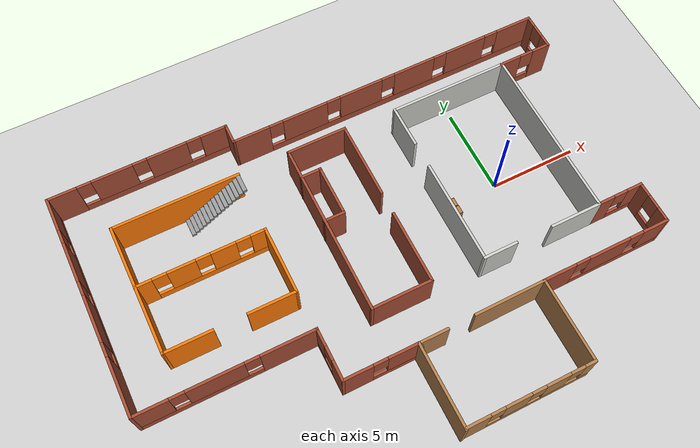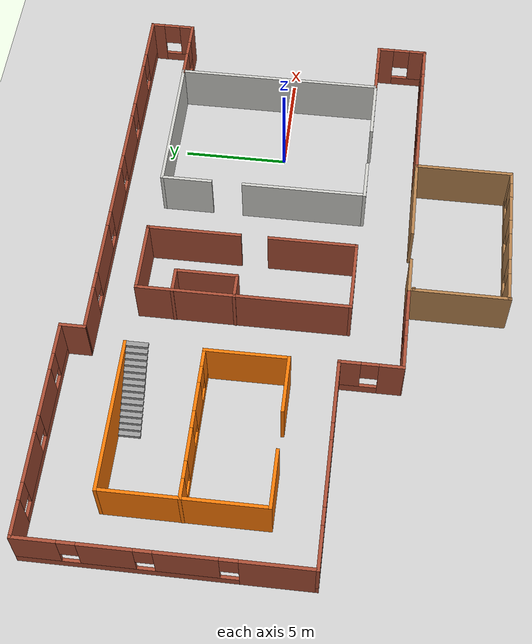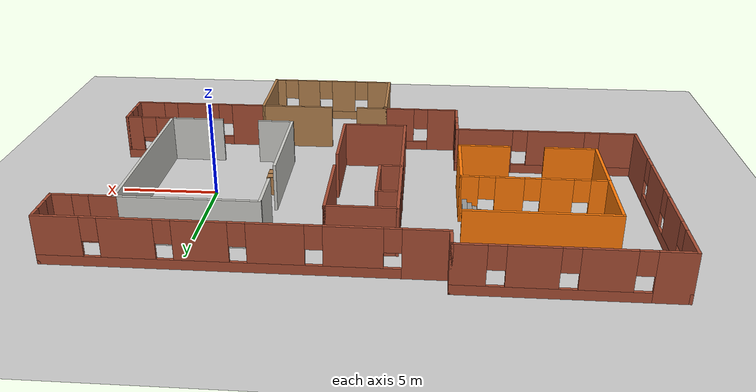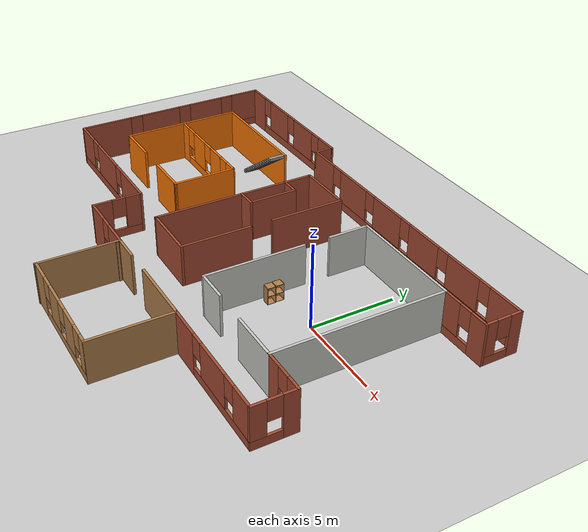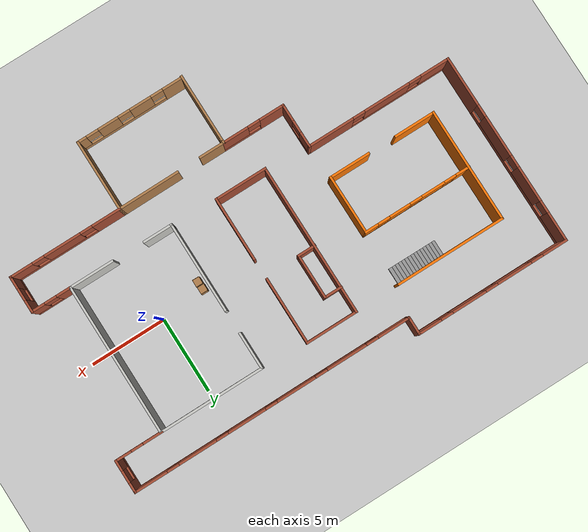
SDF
<sdf version="1.7">
 <world name="default">
  <light name="sun" type="directional">
   <pose>0 0 10 0 -0 0</pose>
   <diffuse>0.8 0.8 0.8 1</diffuse>
   <specular>0.2 0.2 0.2 1</specular>
   <attenuation>
    <range>1000</range>
    <constant>0.9</constant>
    <linear>0.01</linear>
    <quadratic>0.001</quadratic>
   </attenuation>
   <direction>-0.5 0.1 -0.9</direction>
   <spot><inner_angle>0</inner_angle><outer_angle>0</outer_angle><falloff>0</falloff></spot>
  </light>
  <model name="ground_plane">
   <static>1</static>
   <link name="link">
    <collision name="collision">
     <geometry><plane><normal>0 0 1</normal><size>100 100</size></plane></geometry>
     <surface><friction><ode><mu>100</mu><mu2>50</mu2></ode></friction></surface>
    </collision>
    <visual name="visual">
     <cast_shadows>0</cast_shadows>
     <geometry><plane><normal>0 0 1</normal><size>100 100</size></plane></geometry>
     <material>
      <script><uri>file://media/materials/scripts/gazebo.material</uri><name>Gazebo/Grey</name></script>
     </material>
    </visual>
   </link>
  </model>
  <gravity>0 0 -9.8</gravity>
  <magnetic_field>6e-06 2.3e-05 -4.2e-05</magnetic_field>
  <atmosphere type="adiabatic"/>
  <physics type="ode">
   <max_step_size>0.001</max_step_size>
   <real_time_factor>1</real_time_factor>
   <real_time_update_rate>1000</real_time_update_rate>
  </physics>
  <scene><ambient>0.4 0.4 0.4 1</ambient><background>0.7 0.7 0.7 1</background><shadows>1</shadows></scene>
  <audio><device>default</device></audio>
  <spherical_coordinates>
   <surface_model>EARTH_WGS84</surface_model>
   <latitude_deg>0</latitude_deg>
   <longitude_deg>0</longitude_deg>
   <elevation>0</elevation>
   <heading_deg>0</heading_deg>
  </spherical_coordinates>
  <model name="west_2">
   <pose>-7.94174 -1.25517 0 0 -0 0</pose>
   <link name="Stairs_4">
    <visual name="Stairs_4_Visual_0">
     <pose>-8.14297 6.41437 0.083333 0 -0 1.5708</pose>
     <geometry><box><size>1 0.233333 0.166667</size></box></geometry>
     <material>
      <script><uri>file://media/materials/scripts/gazebo.material</uri><name>Gazebo/Grey</name></script>
      <ambient>1 1 1 1</ambient>
     </material>
     <meta><layer>0</layer></meta>
    </visual>
    <collision name="Stairs_4_Collision_0">
     <geometry><box><size>1 0.233333 0.166667</size></box></geometry>
     <pose>-8.14297 6.41437 0.083333 0 -0 1.5708</pose>
    </collision>
    <visual name="Stairs_4_Visual_1">
     <pose>-7.90963 6.41437 0.25 0 -0 1.5708</pose>
     <geometry><box><size>1 0.233333 0.166667</size></box></geometry>
     <material>
      <script><uri>file://media/materials/scripts/gazebo.material</uri><name>Gazebo/Grey</name></script>
      <ambient>1 1 1 1</ambient>
     </material>
     <meta><layer>0</layer></meta>
    </visual>
    <collision name="Stairs_4_Collision_1">
     <geometry><box><size>1 0.233333 0.166667</size></box></geometry>
     <pose>-7.90963 6.41437 0.25 0 -0 1.5708</pose>
    </collision>
    <visual name="Stairs_4_Visual_2">
     <pose>-7.6763 6.41437 0.416667 0 -0 1.5708</pose>
     <geometry><box><size>1 0.233333 0.166667</size></box></geometry>
     <material>
      <script><uri>file://media/materials/scripts/gazebo.material</uri><name>Gazebo/Grey</name></script>
      <ambient>1 1 1 1</ambient>
     </material>
     <meta><layer>0</layer></meta>
    </visual>
    <collision name="Stairs_4_Collision_2">
     <geometry><box><size>1 0.233333 0.166667</size></box></geometry>
     <pose>-7.6763 6.41437 0.416667 0 -0 1.5708</pose>
    </collision>
    <visual name="Stairs_4_Visual_3">
     <pose>-7.44297 6.41437 0.583333 0 -0 1.5708</pose>
     <geometry><box><size>1 0.233333 0.166667</size></box></geometry>
     <material>
      <script><uri>file://media/materials/scripts/gazebo.material</uri><name>Gazebo/Grey</name></script>
      <ambient>1 1 1 1</ambient>
     </material>
     <meta><layer>0</layer></meta>
    </visual>
    <collision name="Stairs_4_Collision_3">
     <geometry><box><size>1 0.233333 0.166667</size></box></geometry>
     <pose>-7.44297 6.41437 0.583333 0 -0 1.5708</pose>
    </collision>
    <visual name="Stairs_4_Visual_4">
     <pose>-7.20963 6.41437 0.75 0 -0 1.5708</pose>
     <geometry><box><size>1 0.233333 0.166667</size></box></geometry>
     <material>
      <script><uri>file://media/materials/scripts/gazebo.material</uri><name>Gazebo/Grey</name></script>
      <ambient>1 1 1 1</ambient>
     </material>
     <meta><layer>0</layer></meta>
    </visual>
    <collision name="Stairs_4_Collision_4">
     <geometry><box><size>1 0.233333 0.166667</size></box></geometry>
     <pose>-7.20963 6.41437 0.75 0 -0 1.5708</pose>
    </collision>
    <visual name="Stairs_4_Visual_5">
     <pose>-6.9763 6.41437 0.916667 0 -0 1.5708</pose>
     <geometry><box><size>1 0.233333 0.166667</size></box></geometry>
     <material>
      <script><uri>file://media/materials/scripts/gazebo.material</uri><name>Gazebo/Grey</name></script>
      <ambient>1 1 1 1</ambient>
     </material>
     <meta><layer>0</layer></meta>
    </visual>
    <collision name="Stairs_4_Collision_5">
     <geometry><box><size>1 0.233333 0.166667</size></box></geometry>
     <pose>-6.9763 6.41437 0.916667 0 -0 1.5708</pose>
    </collision>
    <visual name="Stairs_4_Visual_6">
     <pose>-6.74297 6.41437 1.08333 0 -0 1.5708</pose>
     <geometry><box><size>1 0.233333 0.166667</size></box></geometry>
     <material>
      <script><uri>file://media/materials/scripts/gazebo.material</uri><name>Gazebo/Grey</name></script>
      <ambient>1 1 1 1</ambient>
     </material>
     <meta><layer>0</layer></meta>
    </visual>
    <collision name="Stairs_4_Collision_6">
     <geometry><box><size>1 0.233333 0.166667</size></box></geometry>
     <pose>-6.74297 6.41437 1.08333 0 -0 1.5708</pose>
    </collision>
    <visual name="Stairs_4_Visual_7">
     <pose>-6.50963 6.41437 1.25 0 -0 1.5708</pose>
     <geometry><box><size>1 0.233333 0.166667</size></box></geometry>
     <material>
      <script><uri>file://media/materials/scripts/gazebo.material</uri><name>Gazebo/Grey</name></script>
      <ambient>1 1 1 1</ambient>
     </material>
     <meta><layer>0</layer></meta>
    </visual>
    <collision name="Stairs_4_Collision_7">
     <geometry><box><size>1 0.233333 0.166667</size></box></geometry>
     <pose>-6.50963 6.41437 1.25 0 -0 1.5708</pose>
    </collision>
    <visual name="Stairs_4_Visual_8">
     <pose>-6.2763 6.41437 1.41667 0 -0 1.5708</pose>
     <geometry><box><size>1 0.233333 0.166667</size></box></geometry>
     <material>
      <script><uri>file://media/materials/scripts/gazebo.material</uri><name>Gazebo/Grey</name></script>
      <ambient>1 1 1 1</ambient>
     </material>
     <meta><layer>0</layer></meta>
    </visual>
    <collision name="Stairs_4_Collision_8">
     <geometry><box><size>1 0.233333 0.166667</size></box></geometry>
     <pose>-6.2763 6.41437 1.41667 0 -0 1.5708</pose>
    </collision>
    <visual name="Stairs_4_Visual_9">
     <pose>-6.04297 6.41437 1.58333 0 -0 1.5708</pose>
     <geometry><box><size>1 0.233333 0.166667</size></box></geometry>
     <material>
      <script><uri>file://media/materials/scripts/gazebo.material</uri><name>Gazebo/Grey</name></script>
      <ambient>1 1 1 1</ambient>
     </material>
     <meta><layer>0</layer></meta>
    </visual>
    <collision name="Stairs_4_Collision_9">
     <geometry><box><size>1 0.233333 0.166667</size></box></geometry>
     <pose>-6.04297 6.41437 1.58333 0 -0 1.5708</pose>
    </collision>
    <visual name="Stairs_4_Visual_10">
     <pose>-5.80963 6.41437 1.75 0 -0 1.5708</pose>
     <geometry><box><size>1 0.233333 0.166667</size></box></geometry>
     <material>
      <script><uri>file://media/materials/scripts/gazebo.material</uri><name>Gazebo/Grey</name></script>
      <ambient>1 1 1 1</ambient>
     </material>
     <meta><layer>0</layer></meta>
    </visual>
    <collision name="Stairs_4_Collision_10">
     <geometry><box><size>1 0.233333 0.166667</size></box></geometry>
     <pose>-5.80963 6.41437 1.75 0 -0 1.5708</pose>
    </collision>
    <visual name="Stairs_4_Visual_11">
     <pose>-5.5763 6.41437 1.91667 0 -0 1.5708</pose>
     <geometry><box><size>1 0.233333 0.166667</size></box></geometry>
     <material>
      <script><uri>file://media/materials/scripts/gazebo.material</uri><name>Gazebo/Grey</name></script>
      <ambient>1 1 1 1</ambient>
     </material>
     <meta><layer>0</layer></meta>
    </visual>
    <collision name="Stairs_4_Collision_11">
     <geometry><box><size>1 0.233333 0.166667</size></box></geometry>
     <pose>-5.5763 6.41437 1.91667 0 -0 1.5708</pose>
    </collision>
    <visual name="Stairs_4_Visual_12">
     <pose>-5.34297 6.41437 2.08333 0 -0 1.5708</pose>
     <geometry><box><size>1 0.233333 0.166667</size></box></geometry>
     <material>
      <script><uri>file://media/materials/scripts/gazebo.material</uri><name>Gazebo/Grey</name></script>
      <ambient>1 1 1 1</ambient>
     </material>
     <meta><layer>0</layer></meta>
    </visual>
    <collision name="Stairs_4_Collision_12">
     <geometry><box><size>1 0.233333 0.166667</size></box></geometry>
     <pose>-5.34297 6.41437 2.08333 0 -0 1.5708</pose>
    </collision>
    <visual name="Stairs_4_Visual_13">
     <pose>-5.10963 6.41437 2.25 0 -0 1.5708</pose>
     <geometry><box><size>1 0.233333 0.166667</size></box></geometry>
     <material>
      <script><uri>file://media/materials/scripts/gazebo.material</uri><name>Gazebo/Grey</name></script>
      <ambient>1 1 1 1</ambient>
     </material>
     <meta><layer>0</layer></meta>
    </visual>
    <collision name="Stairs_4_Collision_13">
     <geometry><box><size>1 0.233333 0.166667</size></box></geometry>
     <pose>-5.10963 6.41437 2.25 0 -0 1.5708</pose>
    </collision>
    <visual name="Stairs_4_Visual_14">
     <pose>-4.8763 6.41437 2.41667 0 -0 1.5708</pose>
     <geometry><box><size>1 0.233333 0.166667</size></box></geometry>
     <material>
      <script><uri>file://media/materials/scripts/gazebo.material</uri><name>Gazebo/Grey</name></script>
      <ambient>1 1 1 1</ambient>
     </material>
     <meta><layer>0</layer></meta>
    </visual>
    <collision name="Stairs_4_Collision_14">
     <geometry><box><size>1 0.233333 0.166667</size></box></geometry>
     <pose>-4.8763 6.41437 2.41667 0 -0 1.5708</pose>
    </collision>
   </link>
   <link name="Wall_10">
    <collision name="Wall_10_Collision">
     <geometry><box><size>7 0.15 2.5</size></box></geometry>
     <pose>0 0 1.25 0 -0 0</pose>
    </collision>
    <visual name="Wall_10_Visual">
     <pose>0 0 1.25 0 -0 0</pose>
     <geometry><box><size>7 0.15 2.5</size></box></geometry>
     <material>
      <script><uri>file://media/materials/scripts/gazebo.material</uri><name>Gazebo/CeilingTiled</name></script>
      <ambient>1 1 1 1</ambient>
     </material>
     <meta><layer>0</layer></meta>
    </visual>
    <pose>7.8941 6.82305 0 0 -0 3.14159</pose>
   </link>
   <link name="Wall_11">
    <collision name="Wall_11_Collision">
     <geometry><box><size>2.5 0.15 2.5</size></box></geometry>
     <pose>0 0 1.25 0 -0 0</pose>
    </collision>
    <visual name="Wall_11_Visual">
     <pose>0 0 1.25 0 -0 0</pose>
     <geometry><box><size>2.5 0.15 2.5</size></box></geometry>
     <material>
      <script><uri>file://media/materials/scripts/gazebo.material</uri><name>Gazebo/CeilingTiled</name></script>
      <ambient>1 1 1 1</ambient>
     </material>
     <meta><layer>0</layer></meta>
    </visual>
    <pose>4.4691 5.64805 0 0 -0 -1.5708</pose>
   </link>
   <link name="Wall_14">
    <collision name="Wall_14_Collision">
     <geometry><box><size>2 0.15 2.5</size></box></geometry>
     <pose>0 0 1.25 0 -0 0</pose>
    </collision>
    <visual name="Wall_14_Visual">
     <pose>0 0 1.25 0 -0 0</pose>
     <geometry><box><size>2 0.15 2.5</size></box></geometry>
     <material>
      <script><uri>file://media/materials/scripts/gazebo.material</uri><name>Gazebo/CeilingTiled</name></script>
      <ambient>1 1 1 1</ambient>
     </material>
     <meta><layer>0</layer></meta>
    </visual>
    <pose>5.38836 -2.98607 0 0 -0 3.14159</pose>
   </link>
   <link name="Wall_15">
    <collision name="Wall_15_Collision">
     <geometry><box><size>6 0.15 2.5</size></box></geometry>
     <pose>0 0 1.25 0 -0 0</pose>
    </collision>
    <visual name="Wall_15_Visual">
     <pose>0 0 1.25 0 -0 0</pose>
     <geometry><box><size>6 0.15 2.5</size></box></geometry>
     <material>
      <script><uri>file://media/materials/scripts/gazebo.material</uri><name>Gazebo/CeilingTiled</name></script>
      <ambient>1 1 1 1</ambient>
     </material>
     <meta><layer>0</layer></meta>
    </visual>
    <pose>4.46336 -0.061074 0 0 -0 1.5708</pose>
   </link>
   <link name="Wall_17">
    <pose>12.6191 -3.02695 0 0 -0 0</pose>
    <visual name="Wall_17_Visual_0">
     <pose>-0.864612 0 1.25 0 -0 0</pose>
     <geometry><box><size>1.02078 0.15 2.5</size></box></geometry>
     <material>
      <script><uri>file://media/materials/scripts/gazebo.material</uri><name>Gazebo/Bricks</name></script>
      <ambient>1 1 1 1</ambient>
     </material>
     <meta><layer>0</layer></meta>
    </visual>
    <collision name="Wall_17_Collision_0">
     <geometry><box><size>1.02078 0.15 2.5</size></box></geometry>
     <pose>-0.864612 0 1.25 0 -0 0</pose>
    </collision>
    <visual name="Wall_17_Visual_1">
     <pose>0.510388 0 0.25 0 -0 0</pose>
     <geometry><box><size>1.72922 0.15 0.5</size></box></geometry>
     <material>
      <script><uri>file://media/materials/scripts/gazebo.material</uri><name>Gazebo/Bricks</name></script>
      <ambient>1 1 1 1</ambient>
     </material>
     <meta><layer>0</layer></meta>
    </visual>
    <collision name="Wall_17_Collision_1">
     <geometry><box><size>1.72922 0.15 0.5</size></box></geometry>
     <pose>0.510388 0 0.25 0 -0 0</pose>
    </collision>
    <visual name="Wall_17_Visual_2">
     <pose>0.910388 0 1.5 0 -0 0</pose>
     <geometry><box><size>0.929224 0.15 2</size></box></geometry>
     <material>
      <script><uri>file://media/materials/scripts/gazebo.material</uri><name>Gazebo/Bricks</name></script>
      <ambient>1 1 1 1</ambient>
     </material>
     <meta><layer>0</layer></meta>
    </visual>
    <collision name="Wall_17_Collision_2">
     <geometry><box><size>0.929224 0.15 2</size></box></geometry>
     <pose>0.910388 0 1.5 0 -0 0</pose>
    </collision>
    <visual name="Wall_17_Visual_3">
     <pose>0.045776 0 1.9 0 -0 0</pose>
     <geometry><box><size>0.8 0.15 1.2</size></box></geometry>
     <material>
      <script><uri>file://media/materials/scripts/gazebo.material</uri><name>Gazebo/Bricks</name></script>
      <ambient>1 1 1 1</ambient>
     </material>
     <meta><layer>0</layer></meta>
    </visual>
    <collision name="Wall_17_Collision_3">
     <geometry><box><size>0.8 0.15 1.2</size></box></geometry>
     <pose>0.045776 0 1.9 0 -0 0</pose>
    </collision>
   </link>
   <link name="Wall_18">
    <pose>13.9191 -4.20195 0 0 -0 -1.5708</pose>
    <visual name="Wall_18_Visual_0">
     <pose>-0.829909 0 1.25 0 -0 0</pose>
     <geometry><box><size>0.840181 0.15 2.5</size></box></geometry>
     <material>
      <script><uri>file://media/materials/scripts/gazebo.material</uri><name>Gazebo/Bricks</name></script>
      <ambient>1 1 1 1</ambient>
     </material>
     <meta><layer>0</layer></meta>
    </visual>
    <collision name="Wall_18_Collision_0">
     <geometry><box><size>0.840181 0.15 2.5</size></box></geometry>
     <pose>-0.829909 0 1.25 0 -0 0</pose>
    </collision>
    <visual name="Wall_18_Visual_1">
     <pose>0.420091 0 0.25 0 -0 0</pose>
     <geometry><box><size>1.65982 0.15 0.5</size></box></geometry>
     <material>
      <script><uri>file://media/materials/scripts/gazebo.material</uri><name>Gazebo/Bricks</name></script>
      <ambient>1 1 1 1</ambient>
     </material>
     <meta><layer>0</layer></meta>
    </visual>
    <collision name="Wall_18_Collision_1">
     <geometry><box><size>1.65982 0.15 0.5</size></box></geometry>
     <pose>0.420091 0 0.25 0 -0 0</pose>
    </collision>
    <visual name="Wall_18_Visual_2">
     <pose>0.820091 0 1.5 0 -0 0</pose>
     <geometry><box><size>0.859819 0.15 2</size></box></geometry>
     <material>
      <script><uri>file://media/materials/scripts/gazebo.material</uri><name>Gazebo/Bricks</name></script>
      <ambient>1 1 1 1</ambient>
     </material>
     <meta><layer>0</layer></meta>
    </visual>
    <collision name="Wall_18_Collision_2">
     <geometry><box><size>0.859819 0.15 2</size></box></geometry>
     <pose>0.820091 0 1.5 0 -0 0</pose>
    </collision>
    <visual name="Wall_18_Visual_3">
     <pose>-0.009819 0 1.9 0 -0 0</pose>
     <geometry><box><size>0.8 0.15 1.2</size></box></geometry>
     <material>
      <script><uri>file://media/materials/scripts/gazebo.material</uri><name>Gazebo/Bricks</name></script>
      <ambient>1 1 1 1</ambient>
     </material>
     <meta><layer>0</layer></meta>
    </visual>
    <collision name="Wall_18_Collision_3">
     <geometry><box><size>0.8 0.15 1.2</size></box></geometry>
     <pose>-0.009819 0 1.9 0 -0 0</pose>
    </collision>
   </link>
   <link name="Wall_33">
    <pose>-4.75 -4 0 0 -0 1.5708</pose>
    <visual name="Wall_33_Visual_0">
     <pose>-0.919405 0 1.25 0 -0 0</pose>
     <geometry><box><size>1.16119 0.15 2.5</size></box></geometry>
     <material>
      <script><uri>file://media/materials/scripts/gazebo.material</uri><name>Gazebo/Bricks</name></script>
      <ambient>1 1 1 1</ambient>
     </material>
     <meta><layer>0</layer></meta>
    </visual>
    <collision name="Wall_33_Collision_0">
     <geometry><box><size>1.16119 0.15 2.5</size></box></geometry>
     <pose>-0.919405 0 1.25 0 -0 0</pose>
    </collision>
    <visual name="Wall_33_Visual_1">
     <pose>0.580595 0 0.25 0 -0 0</pose>
     <geometry><box><size>1.83881 0.15 0.5</size></box></geometry>
     <material>
      <script><uri>file://media/materials/scripts/gazebo.material</uri><name>Gazebo/Bricks</name></script>
      <ambient>1 1 1 1</ambient>
     </material>
     <meta><layer>0</layer></meta>
    </visual>
    <collision name="Wall_33_Collision_1">
     <geometry><box><size>1.83881 0.15 0.5</size></box></geometry>
     <pose>0.580595 0 0.25 0 -0 0</pose>
    </collision>
    <visual name="Wall_33_Visual_2">
     <pose>0.980595 0 1.5 0 -0 0</pose>
     <geometry><box><size>1.03881 0.15 2</size></box></geometry>
     <material>
      <script><uri>file://media/materials/scripts/gazebo.material</uri><name>Gazebo/Bricks</name></script>
      <ambient>1 1 1 1</ambient>
     </material>
     <meta><layer>0</layer></meta>
    </visual>
    <collision name="Wall_33_Collision_2">
     <geometry><box><size>1.03881 0.15 2</size></box></geometry>
     <pose>0.980595 0 1.5 0 -0 0</pose>
    </collision>
    <visual name="Wall_33_Visual_3">
     <pose>0.06119 0 1.9 0 -0 0</pose>
     <geometry><box><size>0.8 0.15 1.2</size></box></geometry>
     <material>
      <script><uri>file://media/materials/scripts/gazebo.material</uri><name>Gazebo/Bricks</name></script>
      <ambient>1 1 1 1</ambient>
     </material>
     <meta><layer>0</layer></meta>
    </visual>
    <collision name="Wall_33_Collision_3">
     <geometry><box><size>0.8 0.15 1.2</size></box></geometry>
     <pose>0.06119 0 1.9 0 -0 0</pose>
    </collision>
   </link>
   <link name="Wall_34">
    <pose>-9.55 -2.575 0 0 -0 3.14159</pose>
    <visual name="Wall_34_Visual_0">
     <pose>-3.32251 0 1.25 0 -0 0</pose>
     <geometry><box><size>3.10499 0.15 2.5</size></box></geometry>
     <material>
      <script><uri>file://media/materials/scripts/gazebo.material</uri><name>Gazebo/Bricks</name></script>
      <ambient>1 1 1 1</ambient>
     </material>
     <meta><layer>0</layer></meta>
    </visual>
    <collision name="Wall_34_Collision_0">
     <geometry><box><size>3.10499 0.15 2.5</size></box></geometry>
     <pose>-3.32251 0 1.25 0 -0 0</pose>
    </collision>
    <visual name="Wall_34_Visual_1">
     <pose>1.55249 0 0.25 0 -0 0</pose>
     <geometry><box><size>6.64501 0.15 0.5</size></box></geometry>
     <material>
      <script><uri>file://media/materials/scripts/gazebo.material</uri><name>Gazebo/Bricks</name></script>
      <ambient>1 1 1 1</ambient>
     </material>
     <meta><layer>0</layer></meta>
    </visual>
    <collision name="Wall_34_Collision_1">
     <geometry><box><size>6.64501 0.15 0.5</size></box></geometry>
     <pose>1.55249 0 0.25 0 -0 0</pose>
    </collision>
    <visual name="Wall_34_Visual_2">
     <pose>0.566097 0 1.5 0 -0 0</pose>
     <geometry><box><size>3.07222 0.15 2</size></box></geometry>
     <material>
      <script><uri>file://media/materials/scripts/gazebo.material</uri><name>Gazebo/Bricks</name></script>
      <ambient>1 1 1 1</ambient>
     </material>
     <meta><layer>0</layer></meta>
    </visual>
    <collision name="Wall_34_Collision_2">
     <geometry><box><size>3.07222 0.15 2</size></box></geometry>
     <pose>0.566097 0 1.5 0 -0 0</pose>
    </collision>
    <visual name="Wall_34_Visual_3">
     <pose>3.8886 0 1.5 0 -0 0</pose>
     <geometry><box><size>1.97279 0.15 2</size></box></geometry>
     <material>
      <script><uri>file://media/materials/scripts/gazebo.material</uri><name>Gazebo/Bricks</name></script>
      <ambient>1 1 1 1</ambient>
     </material>
     <meta><layer>0</layer></meta>
    </visual>
    <collision name="Wall_34_Collision_3">
     <geometry><box><size>1.97279 0.15 2</size></box></geometry>
     <pose>3.8886 0 1.5 0 -0 0</pose>
    </collision>
    <visual name="Wall_34_Visual_4">
     <pose>-1.37001 0 1.9 0 -0 0</pose>
     <geometry><box><size>0.8 0.15 1.2</size></box></geometry>
     <material>
      <script><uri>file://media/materials/scripts/gazebo.material</uri><name>Gazebo/Bricks</name></script>
      <ambient>1 1 1 1</ambient>
     </material>
     <meta><layer>0</layer></meta>
    </visual>
    <collision name="Wall_34_Collision_4">
     <geometry><box><size>0.8 0.15 1.2</size></box></geometry>
     <pose>-1.37001 0 1.9 0 -0 0</pose>
    </collision>
    <visual name="Wall_34_Visual_5">
     <pose>2.50221 0 1.9 0 -0 0</pose>
     <geometry><box><size>0.8 0.15 1.2</size></box></geometry>
     <material>
      <script><uri>file://media/materials/scripts/gazebo.material</uri><name>Gazebo/Bricks</name></script>
      <ambient>1 1 1 1</ambient>
     </material>
     <meta><layer>0</layer></meta>
    </visual>
    <collision name="Wall_34_Collision_5">
     <geometry><box><size>0.8 0.15 1.2</size></box></geometry>
     <pose>2.50221 0 1.9 0 -0 0</pose>
    </collision>
   </link>
   <link name="Wall_35">
    <pose>-14.35 3.725 0 0 -0 1.5708</pose>
    <visual name="Wall_35_Visual_0">
     <pose>-4.72236 0 1.25 0 -0 0</pose>
     <geometry><box><size>3.30527 0.15 2.5</size></box></geometry>
     <material>
      <script><uri>file://media/materials/scripts/gazebo.material</uri><name>Gazebo/Bricks</name></script>
      <ambient>1 1 1 1</ambient>
     </material>
     <meta><layer>0</layer></meta>
    </visual>
    <collision name="Wall_35_Collision_0">
     <geometry><box><size>3.30527 0.15 2.5</size></box></geometry>
     <pose>-4.72236 0 1.25 0 -0 0</pose>
    </collision>
    <visual name="Wall_35_Visual_1">
     <pose>1.65264 0 0.25 0 -0 0</pose>
     <geometry><box><size>9.44473 0.15 0.5</size></box></geometry>
     <material>
      <script><uri>file://media/materials/scripts/gazebo.material</uri><name>Gazebo/Bricks</name></script>
      <ambient>1 1 1 1</ambient>
     </material>
     <meta><layer>0</layer></meta>
    </visual>
    <collision name="Wall_35_Collision_1">
     <geometry><box><size>9.44473 0.15 0.5</size></box></geometry>
     <pose>1.65264 0 0.25 0 -0 0</pose>
    </collision>
    <visual name="Wall_35_Visual_2">
     <pose>-0.914561 0 1.5 0 -0 0</pose>
     <geometry><box><size>2.71033 0.15 2</size></box></geometry>
     <material>
      <script><uri>file://media/materials/scripts/gazebo.material</uri><name>Gazebo/Bricks</name></script>
      <ambient>1 1 1 1</ambient>
     </material>
     <meta><layer>0</layer></meta>
    </visual>
    <collision name="Wall_35_Collision_2">
     <geometry><box><size>2.71033 0.15 2</size></box></geometry>
     <pose>-0.914561 0 1.5 0 -0 0</pose>
    </collision>
    <visual name="Wall_35_Visual_3">
     <pose>2.41483 0 1.5 0 -0 0</pose>
     <geometry><box><size>2.34844 0.15 2</size></box></geometry>
     <material>
      <script><uri>file://media/materials/scripts/gazebo.material</uri><name>Gazebo/Bricks</name></script>
      <ambient>1 1 1 1</ambient>
     </material>
     <meta><layer>0</layer></meta>
    </visual>
    <collision name="Wall_35_Collision_3">
     <geometry><box><size>2.34844 0.15 2</size></box></geometry>
     <pose>2.41483 0 1.5 0 -0 0</pose>
    </collision>
    <visual name="Wall_35_Visual_4">
     <pose>5.38202 0 1.5 0 -0 0</pose>
     <geometry><box><size>1.98595 0.15 2</size></box></geometry>
     <material>
      <script><uri>file://media/materials/scripts/gazebo.material</uri><name>Gazebo/Bricks</name></script>
      <ambient>1 1 1 1</ambient>
     </material>
     <meta><layer>0</layer></meta>
    </visual>
    <collision name="Wall_35_Collision_4">
     <geometry><box><size>1.98595 0.15 2</size></box></geometry>
     <pose>5.38202 0 1.5 0 -0 0</pose>
    </collision>
    <visual name="Wall_35_Visual_5">
     <pose>-2.66973 0 1.9 0 -0 0</pose>
     <geometry><box><size>0.8 0.15 1.2</size></box></geometry>
     <material>
      <script><uri>file://media/materials/scripts/gazebo.material</uri><name>Gazebo/Bricks</name></script>
      <ambient>1 1 1 1</ambient>
     </material>
     <meta><layer>0</layer></meta>
    </visual>
    <collision name="Wall_35_Collision_5">
     <geometry><box><size>0.8 0.15 1.2</size></box></geometry>
     <pose>-2.66973 0 1.9 0 -0 0</pose>
    </collision>
    <visual name="Wall_35_Visual_6">
     <pose>0.840605 0 1.9 0 -0 0</pose>
     <geometry><box><size>0.8 0.15 1.2</size></box></geometry>
     <material>
      <script><uri>file://media/materials/scripts/gazebo.material</uri><name>Gazebo/Bricks</name></script>
      <ambient>1 1 1 1</ambient>
     </material>
     <meta><layer>0</layer></meta>
    </visual>
    <collision name="Wall_35_Collision_6">
     <geometry><box><size>0.8 0.15 1.2</size></box></geometry>
     <pose>0.840605 0 1.9 0 -0 0</pose>
    </collision>
    <visual name="Wall_35_Visual_7">
     <pose>3.98905 0 1.9 0 -0 0</pose>
     <geometry><box><size>0.8 0.15 1.2</size></box></geometry>
     <material>
      <script><uri>file://media/materials/scripts/gazebo.material</uri><name>Gazebo/Bricks</name></script>
      <ambient>1 1 1 1</ambient>
     </material>
     <meta><layer>0</layer></meta>
    </visual>
    <collision name="Wall_35_Collision_7">
     <geometry><box><size>0.8 0.15 1.2</size></box></geometry>
     <pose>3.98905 0 1.9 0 -0 0</pose>
    </collision>
   </link>
   <link name="Wall_36">
    <pose>-9.3 10.025 0 0 -0 0</pose>
    <visual name="Wall_36_Visual_0">
     <pose>-4.28336 0 1.25 0 -0 0</pose>
     <geometry><box><size>1.68328 0.15 2.5</size></box></geometry>
     <material>
      <script><uri>file://media/materials/scripts/gazebo.material</uri><name>Gazebo/Bricks</name></script>
      <ambient>1 1 1 1</ambient>
     </material>
     <meta><layer>0</layer></meta>
    </visual>
    <collision name="Wall_36_Collision_0">
     <geometry><box><size>1.68328 0.15 2.5</size></box></geometry>
     <pose>-4.28336 0 1.25 0 -0 0</pose>
    </collision>
    <visual name="Wall_36_Visual_1">
     <pose>0.841639 0 0.25 0 -0 0</pose>
     <geometry><box><size>8.56672 0.15 0.5</size></box></geometry>
     <material>
      <script><uri>file://media/materials/scripts/gazebo.material</uri><name>Gazebo/Bricks</name></script>
      <ambient>1 1 1 1</ambient>
     </material>
     <meta><layer>0</layer></meta>
    </visual>
    <collision name="Wall_36_Collision_1">
     <geometry><box><size>8.56672 0.15 0.5</size></box></geometry>
     <pose>0.841639 0 0.25 0 -0 0</pose>
    </collision>
    <visual name="Wall_36_Visual_2">
     <pose>-1.48559 0 1.5 0 -0 0</pose>
     <geometry><box><size>2.31225 0.15 2</size></box></geometry>
     <material>
      <script><uri>file://media/materials/scripts/gazebo.material</uri><name>Gazebo/Bricks</name></script>
      <ambient>1 1 1 1</ambient>
     </material>
     <meta><layer>0</layer></meta>
    </visual>
    <collision name="Wall_36_Collision_2">
     <geometry><box><size>2.31225 0.15 2</size></box></geometry>
     <pose>-1.48559 0 1.5 0 -0 0</pose>
    </collision>
    <visual name="Wall_36_Visual_3">
     <pose>1.60857 0 1.5 0 -0 0</pose>
     <geometry><box><size>2.27606 0.15 2</size></box></geometry>
     <material>
      <script><uri>file://media/materials/scripts/gazebo.material</uri><name>Gazebo/Bricks</name></script>
      <ambient>1 1 1 1</ambient>
     </material>
     <meta><layer>0</layer></meta>
    </visual>
    <collision name="Wall_36_Collision_3">
     <geometry><box><size>2.27606 0.15 2</size></box></geometry>
     <pose>1.60857 0 1.5 0 -0 0</pose>
    </collision>
    <visual name="Wall_36_Visual_4">
     <pose>4.3358 0 1.5 0 -0 0</pose>
     <geometry><box><size>1.5784 0.15 2</size></box></geometry>
     <material>
      <script><uri>file://media/materials/scripts/gazebo.material</uri><name>Gazebo/Bricks</name></script>
      <ambient>1 1 1 1</ambient>
     </material>
     <meta><layer>0</layer></meta>
    </visual>
    <collision name="Wall_36_Collision_4">
     <geometry><box><size>1.5784 0.15 2</size></box></geometry>
     <pose>4.3358 0 1.5 0 -0 0</pose>
    </collision>
    <visual name="Wall_36_Visual_5">
     <pose>-3.04172 0 1.9 0 -0 0</pose>
     <geometry><box><size>0.8 0.15 1.2</size></box></geometry>
     <material>
      <script><uri>file://media/materials/scripts/gazebo.material</uri><name>Gazebo/Bricks</name></script>
      <ambient>1 1 1 1</ambient>
     </material>
     <meta><layer>0</layer></meta>
    </visual>
    <collision name="Wall_36_Collision_5">
     <geometry><box><size>0.8 0.15 1.2</size></box></geometry>
     <pose>-3.04172 0 1.9 0 -0 0</pose>
    </collision>
    <visual name="Wall_36_Visual_6">
     <pose>0.070534 0 1.9 0 -0 0</pose>
     <geometry><box><size>0.8 0.15 1.2</size></box></geometry>
     <material>
      <script><uri>file://media/materials/scripts/gazebo.material</uri><name>Gazebo/Bricks</name></script>
      <ambient>1 1 1 1</ambient>
     </material>
     <meta><layer>0</layer></meta>
    </visual>
    <collision name="Wall_36_Collision_6">
     <geometry><box><size>0.8 0.15 1.2</size></box></geometry>
     <pose>0.070534 0 1.9 0 -0 0</pose>
    </collision>
    <visual name="Wall_36_Visual_7">
     <pose>3.1466 0 1.9 0 -0 0</pose>
     <geometry><box><size>0.8 0.15 1.2</size></box></geometry>
     <material>
      <script><uri>file://media/materials/scripts/gazebo.material</uri><name>Gazebo/Bricks</name></script>
      <ambient>1 1 1 1</ambient>
     </material>
     <meta><layer>0</layer></meta>
    </visual>
    <collision name="Wall_36_Collision_7">
     <geometry><box><size>0.8 0.15 1.2</size></box></geometry>
     <pose>3.1466 0 1.9 0 -0 0</pose>
    </collision>
   </link>
   <link name="Wall_37">
    <collision name="Wall_37_Collision">
     <geometry><box><size>1.25 0.15 2.5</size></box></geometry>
     <pose>0 0 1.25 0 -0 0</pose>
    </collision>
    <visual name="Wall_37_Visual">
     <pose>0 0 1.25 0 -0 0</pose>
     <geometry><box><size>1.25 0.15 2.5</size></box></geometry>
     <material>
      <script><uri>file://media/materials/scripts/gazebo.material</uri><name>Gazebo/Bricks</name></script>
      <ambient>1 1 1 1</ambient>
     </material>
     <meta><layer>0</layer></meta>
    </visual>
    <pose>-4.25 9.475 0 0 -0 -1.5708</pose>
   </link>
   <link name="Wall_38">
    <pose>5.05 8.925 0 0 -0 0</pose>
    <visual name="Wall_38_Visual_0">
     <pose>-8.28167 0 1.25 0 -0 0</pose>
     <geometry><box><size>2.18666 0.15 2.5</size></box></geometry>
     <material>
      <script><uri>file://media/materials/scripts/gazebo.material</uri><name>Gazebo/Bricks</name></script>
      <ambient>1 1 1 1</ambient>
     </material>
     <meta><layer>0</layer></meta>
    </visual>
    <collision name="Wall_38_Collision_0">
     <geometry><box><size>2.18666 0.15 2.5</size></box></geometry>
     <pose>-8.28167 0 1.25 0 -0 0</pose>
    </collision>
    <visual name="Wall_38_Visual_1">
     <pose>1.09333 0 0.25 0 -0 0</pose>
     <geometry><box><size>16.5633 0.15 0.5</size></box></geometry>
     <material>
      <script><uri>file://media/materials/scripts/gazebo.material</uri><name>Gazebo/Bricks</name></script>
      <ambient>1 1 1 1</ambient>
     </material>
     <meta><layer>0</layer></meta>
    </visual>
    <collision name="Wall_38_Collision_1">
     <geometry><box><size>16.5633 0.15 0.5</size></box></geometry>
     <pose>1.09333 0 0.25 0 -0 0</pose>
    </collision>
    <visual name="Wall_38_Visual_2">
     <pose>-5.05127 0 1.5 0 -0 0</pose>
     <geometry><box><size>2.67414 0.15 2</size></box></geometry>
     <material>
      <script><uri>file://media/materials/scripts/gazebo.material</uri><name>Gazebo/Bricks</name></script>
      <ambient>1 1 1 1</ambient>
     </material>
     <meta><layer>0</layer></meta>
    </visual>
    <collision name="Wall_38_Collision_2">
     <geometry><box><size>2.67414 0.15 2</size></box></geometry>
     <pose>-5.05127 0 1.5 0 -0 0</pose>
    </collision>
    <visual name="Wall_38_Visual_3">
     <pose>-1.61332 0 1.5 0 -0 0</pose>
     <geometry><box><size>2.60177 0.15 2</size></box></geometry>
     <material>
      <script><uri>file://media/materials/scripts/gazebo.material</uri><name>Gazebo/Bricks</name></script>
      <ambient>1 1 1 1</ambient>
     </material>
     <meta><layer>0</layer></meta>
    </visual>
    <collision name="Wall_38_Collision_3">
     <geometry><box><size>2.60177 0.15 2</size></box></geometry>
     <pose>-1.61332 0 1.5 0 -0 0</pose>
    </collision>
    <visual name="Wall_38_Visual_4">
     <pose>1.75226 0 1.5 0 -0 0</pose>
     <geometry><box><size>2.52939 0.15 2</size></box></geometry>
     <material>
      <script><uri>file://media/materials/scripts/gazebo.material</uri><name>Gazebo/Bricks</name></script>
      <ambient>1 1 1 1</ambient>
     </material>
     <meta><layer>0</layer></meta>
    </visual>
    <collision name="Wall_38_Collision_4">
     <geometry><box><size>2.52939 0.15 2</size></box></geometry>
     <pose>1.75226 0 1.5 0 -0 0</pose>
    </collision>
    <visual name="Wall_38_Visual_5">
     <pose>5.08165 0 1.5 0 -0 0</pose>
     <geometry><box><size>2.52939 0.15 2</size></box></geometry>
     <material>
      <script><uri>file://media/materials/scripts/gazebo.material</uri><name>Gazebo/Bricks</name></script>
      <ambient>1 1 1 1</ambient>
     </material>
     <meta><layer>0</layer></meta>
    </visual>
    <collision name="Wall_38_Collision_5">
     <geometry><box><size>2.52939 0.15 2</size></box></geometry>
     <pose>5.08165 0 1.5 0 -0 0</pose>
    </collision>
    <visual name="Wall_38_Visual_6">
     <pose>8.26067 0 1.5 0 -0 0</pose>
     <geometry><box><size>2.22866 0.15 2</size></box></geometry>
     <material>
      <script><uri>file://media/materials/scripts/gazebo.material</uri><name>Gazebo/Bricks</name></script>
      <ambient>1 1 1 1</ambient>
     </material>
     <meta><layer>0</layer></meta>
    </visual>
    <collision name="Wall_38_Collision_6">
     <geometry><box><size>2.22866 0.15 2</size></box></geometry>
     <pose>8.26067 0 1.5 0 -0 0</pose>
    </collision>
    <visual name="Wall_38_Visual_7">
     <pose>-6.78834 0 1.9 0 -0 0</pose>
     <geometry><box><size>0.8 0.15 1.2</size></box></geometry>
     <material>
      <script><uri>file://media/materials/scripts/gazebo.material</uri><name>Gazebo/Bricks</name></script>
      <ambient>1 1 1 1</ambient>
     </material>
     <meta><layer>0</layer></meta>
    </visual>
    <collision name="Wall_38_Collision_7">
     <geometry><box><size>0.8 0.15 1.2</size></box></geometry>
     <pose>-6.78834 0 1.9 0 -0 0</pose>
    </collision>
    <visual name="Wall_38_Visual_8">
     <pose>-3.3142 0 1.9 0 -0 0</pose>
     <geometry><box><size>0.8 0.15 1.2</size></box></geometry>
     <material>
      <script><uri>file://media/materials/scripts/gazebo.material</uri><name>Gazebo/Bricks</name></script>
      <ambient>1 1 1 1</ambient>
     </material>
     <meta><layer>0</layer></meta>
    </visual>
    <collision name="Wall_38_Collision_8">
     <geometry><box><size>0.8 0.15 1.2</size></box></geometry>
     <pose>-3.3142 0 1.9 0 -0 0</pose>
    </collision>
    <visual name="Wall_38_Visual_9">
     <pose>0.087566 0 1.9 0 -0 0</pose>
     <geometry><box><size>0.8 0.15 1.2</size></box></geometry>
     <material>
      <script><uri>file://media/materials/scripts/gazebo.material</uri><name>Gazebo/Bricks</name></script>
      <ambient>1 1 1 1</ambient>
     </material>
     <meta><layer>0</layer></meta>
    </visual>
    <collision name="Wall_38_Collision_9">
     <geometry><box><size>0.8 0.15 1.2</size></box></geometry>
     <pose>0.087566 0 1.9 0 -0 0</pose>
    </collision>
    <visual name="Wall_38_Visual_10">
     <pose>3.41695 0 1.9 0 -0 0</pose>
     <geometry><box><size>0.8 0.15 1.2</size></box></geometry>
     <material>
      <script><uri>file://media/materials/scripts/gazebo.material</uri><name>Gazebo/Bricks</name></script>
      <ambient>1 1 1 1</ambient>
     </material>
     <meta><layer>0</layer></meta>
    </visual>
    <collision name="Wall_38_Collision_10">
     <geometry><box><size>0.8 0.15 1.2</size></box></geometry>
     <pose>3.41695 0 1.9 0 -0 0</pose>
    </collision>
    <visual name="Wall_38_Visual_11">
     <pose>6.74634 0 1.9 0 -0 0</pose>
     <geometry><box><size>0.8 0.15 1.2</size></box></geometry>
     <material>
      <script><uri>file://media/materials/scripts/gazebo.material</uri><name>Gazebo/Bricks</name></script>
      <ambient>1 1 1 1</ambient>
     </material>
     <meta><layer>0</layer></meta>
    </visual>
    <collision name="Wall_38_Collision_11">
     <geometry><box><size>0.8 0.15 1.2</size></box></geometry>
     <pose>6.74634 0 1.9 0 -0 0</pose>
    </collision>
   </link>
   <link name="Wall_39">
    <pose>14.35 7.875 0 0 -0 -1.5708</pose>
    <visual name="Wall_39_Visual_0">
     <pose>-0.772497 0 1.25 0 -0 0</pose>
     <geometry><box><size>0.705007 0.15 2.5</size></box></geometry>
     <material>
      <script><uri>file://media/materials/scripts/gazebo.material</uri><name>Gazebo/Bricks</name></script>
      <ambient>1 1 1 1</ambient>
     </material>
     <meta><layer>0</layer></meta>
    </visual>
    <collision name="Wall_39_Collision_0">
     <geometry><box><size>0.705007 0.15 2.5</size></box></geometry>
     <pose>-0.772497 0 1.25 0 -0 0</pose>
    </collision>
    <visual name="Wall_39_Visual_1">
     <pose>0.352503 0 0.25 0 -0 0</pose>
     <geometry><box><size>1.54499 0.15 0.5</size></box></geometry>
     <material>
      <script><uri>file://media/materials/scripts/gazebo.material</uri><name>Gazebo/Bricks</name></script>
      <ambient>1 1 1 1</ambient>
     </material>
     <meta><layer>0</layer></meta>
    </visual>
    <collision name="Wall_39_Collision_1">
     <geometry><box><size>1.54499 0.15 0.5</size></box></geometry>
     <pose>0.352503 0 0.25 0 -0 0</pose>
    </collision>
    <visual name="Wall_39_Visual_2">
     <pose>0.752503 0 1.5 0 -0 0</pose>
     <geometry><box><size>0.744993 0.15 2</size></box></geometry>
     <material>
      <script><uri>file://media/materials/scripts/gazebo.material</uri><name>Gazebo/Bricks</name></script>
      <ambient>1 1 1 1</ambient>
     </material>
     <meta><layer>0</layer></meta>
    </visual>
    <collision name="Wall_39_Collision_2">
     <geometry><box><size>0.744993 0.15 2</size></box></geometry>
     <pose>0.752503 0 1.5 0 -0 0</pose>
    </collision>
    <visual name="Wall_39_Visual_3">
     <pose>-0.019993 0 1.9 0 -0 0</pose>
     <geometry><box><size>0.8 0.15 1.2</size></box></geometry>
     <material>
      <script><uri>file://media/materials/scripts/gazebo.material</uri><name>Gazebo/Bricks</name></script>
      <ambient>1 1 1 1</ambient>
     </material>
     <meta><layer>0</layer></meta>
    </visual>
    <collision name="Wall_39_Collision_3">
     <geometry><box><size>0.8 0.15 1.2</size></box></geometry>
     <pose>-0.019993 0 1.9 0 -0 0</pose>
    </collision>
   </link>
   <link name="Wall_4">
    <collision name="Wall_4_Collision">
     <geometry><box><size>10 0.15 2.5</size></box></geometry>
     <pose>0 0 1.25 0 -0 0</pose>
    </collision>
    <visual name="Wall_4_Visual">
     <pose>0 0 1.25 0 -0 0</pose>
     <geometry><box><size>10 0.15 2.5</size></box></geometry>
     <material>
      <script><uri>file://media/materials/scripts/gazebo.material</uri><name>Gazebo/CeilingTiled</name></script>
      <ambient>1 1 1 1</ambient>
     </material>
     <meta><layer>0</layer></meta>
    </visual>
    <pose>11.3191 1.89805 0 0 -0 -1.5708</pose>
   </link>
   <link name="Wall_40">
    <pose>12.8 6.825 0 0 -0 3.14159</pose>
    <visual name="Wall_40_Visual_0">
     <pose>-1.0716 0 1.25 0 -0 0</pose>
     <geometry><box><size>1.1068 0.15 2.5</size></box></geometry>
     <material>
      <script><uri>file://media/materials/scripts/gazebo.material</uri><name>Gazebo/Bricks</name></script>
      <ambient>1 1 1 1</ambient>
     </material>
     <meta><layer>0</layer></meta>
    </visual>
    <collision name="Wall_40_Collision_0">
     <geometry><box><size>1.1068 0.15 2.5</size></box></geometry>
     <pose>-1.0716 0 1.25 0 -0 0</pose>
    </collision>
    <visual name="Wall_40_Visual_1">
     <pose>0.5534 0 0.25 0 -0 0</pose>
     <geometry><box><size>2.1432 0.15 0.5</size></box></geometry>
     <material>
      <script><uri>file://media/materials/scripts/gazebo.material</uri><name>Gazebo/Bricks</name></script>
      <ambient>1 1 1 1</ambient>
     </material>
     <meta><layer>0</layer></meta>
    </visual>
    <collision name="Wall_40_Collision_1">
     <geometry><box><size>2.1432 0.15 0.5</size></box></geometry>
     <pose>0.5534 0 0.25 0 -0 0</pose>
    </collision>
    <visual name="Wall_40_Visual_2">
     <pose>0.9534 0 1.5 0 -0 0</pose>
     <geometry><box><size>1.3432 0.15 2</size></box></geometry>
     <material>
      <script><uri>file://media/materials/scripts/gazebo.material</uri><name>Gazebo/Bricks</name></script>
      <ambient>1 1 1 1</ambient>
     </material>
     <meta><layer>0</layer></meta>
    </visual>
    <collision name="Wall_40_Collision_2">
     <geometry><box><size>1.3432 0.15 2</size></box></geometry>
     <pose>0.9534 0 1.5 0 -0 0</pose>
    </collision>
    <visual name="Wall_40_Visual_3">
     <pose>-0.118201 0 1.9 0 -0 0</pose>
     <geometry><box><size>0.8 0.15 1.2</size></box></geometry>
     <material>
      <script><uri>file://media/materials/scripts/gazebo.material</uri><name>Gazebo/Bricks</name></script>
      <ambient>1 1 1 1</ambient>
     </material>
     <meta><layer>0</layer></meta>
    </visual>
    <collision name="Wall_40_Collision_3">
     <geometry><box><size>0.8 0.15 1.2</size></box></geometry>
     <pose>-0.118201 0 1.9 0 -0 0</pose>
    </collision>
   </link>
   <link name="Wall_43">
    <collision name="Wall_43_Collision">
     <geometry><box><size>4.25 0.15 2.5</size></box></geometry>
     <pose>0 0 1.25 0 -0 0</pose>
    </collision>
    <visual name="Wall_43_Visual">
     <pose>0 0 1.25 0 -0 0</pose>
     <geometry><box><size>4.25 0.15 2.5</size></box></geometry>
     <material>
      <script><uri>file://media/materials/scripts/gazebo.material</uri><name>Gazebo/Bricks</name></script>
      <ambient>1 1 1 1</ambient>
     </material>
     <meta><layer>0</layer></meta>
    </visual>
    <pose>1.47586 -0.796539 0 0 -0 -1.5708</pose>
   </link>
   <link name="Wall_44">
    <collision name="Wall_44_Collision">
     <geometry><box><size>3.5 0.15 2.5</size></box></geometry>
     <pose>0 0 1.25 0 -0 0</pose>
    </collision>
    <visual name="Wall_44_Visual">
     <pose>0 0 1.25 0 -0 0</pose>
     <geometry><box><size>3.5 0.15 2.5</size></box></geometry>
     <material>
      <script><uri>file://media/materials/scripts/gazebo.material</uri><name>Gazebo/Bricks</name></script>
      <ambient>1 1 1 1</ambient>
     </material>
     <meta><layer>0</layer></meta>
    </visual>
    <pose>-0.199136 -2.84654 0 0 -0 3.14159</pose>
   </link>
   <link name="Wall_45">
    <collision name="Wall_45_Collision">
     <geometry><box><size>10 0.15 2.5</size></box></geometry>
     <pose>0 0 1.25 0 -0 0</pose>
    </collision>
    <visual name="Wall_45_Visual">
     <pose>0 0 1.25 0 -0 0</pose>
     <geometry><box><size>10 0.15 2.5</size></box></geometry>
     <material>
      <script><uri>file://media/materials/scripts/gazebo.material</uri><name>Gazebo/Bricks</name></script>
      <ambient>1 1 1 1</ambient>
     </material>
     <meta><layer>0</layer></meta>
    </visual>
    <pose>-1.87414 2.07846 0 0 -0 1.5708</pose>
   </link>
   <link name="Wall_46">
    <collision name="Wall_46_Collision">
     <geometry><box><size>3.5 0.15 2.5</size></box></geometry>
     <pose>0 0 1.25 0 -0 0</pose>
    </collision>
    <visual name="Wall_46_Visual">
     <pose>0 0 1.25 0 -0 0</pose>
     <geometry><box><size>3.5 0.15 2.5</size></box></geometry>
     <material>
      <script><uri>file://media/materials/scripts/gazebo.material</uri><name>Gazebo/Bricks</name></script>
      <ambient>1 1 1 1</ambient>
     </material>
     <meta><layer>0</layer></meta>
    </visual>
    <pose>-0.199136 7.00346 0 0 -0 0</pose>
   </link>
   <link name="Wall_47">
    <collision name="Wall_47_Collision">
     <geometry><box><size>4.5 0.15 2.5</size></box></geometry>
     <pose>0 0 1.25 0 -0 0</pose>
    </collision>
    <visual name="Wall_47_Visual">
     <pose>0 0 1.25 0 -0 0</pose>
     <geometry><box><size>4.5 0.15 2.5</size></box></geometry>
     <material>
      <script><uri>file://media/materials/scripts/gazebo.material</uri><name>Gazebo/Bricks</name></script>
      <ambient>1 1 1 1</ambient>
     </material>
     <meta><layer>0</layer></meta>
    </visual>
    <pose>1.47586 4.82846 0 0 -0 -1.5708</pose>
   </link>
   <link name="Wall_50">
    <collision name="Wall_50_Collision">
     <geometry><box><size>1.25 0.15 2.5</size></box></geometry>
     <pose>0 0 1.25 0 -0 0</pose>
    </collision>
    <visual name="Wall_50_Visual">
     <pose>0 0 1.25 0 -0 0</pose>
     <geometry><box><size>1.25 0.15 2.5</size></box></geometry>
     <material>
      <script><uri>file://media/materials/scripts/gazebo.material</uri><name>Gazebo/Bricks</name></script>
      <ambient>1 1 1 1</ambient>
     </material>
     <meta><layer>0</layer></meta>
    </visual>
    <pose>-1.34332 5.33184 0 0 -0 0</pose>
   </link>
   <link name="Wall_51">
    <collision name="Wall_51_Collision">
     <geometry><box><size>3 0.15 2.5</size></box></geometry>
     <pose>0 0 1.25 0 -0 0</pose>
    </collision>
    <visual name="Wall_51_Visual">
     <pose>0 0 1.25 0 -0 0</pose>
     <geometry><box><size>3 0.15 2.5</size></box></geometry>
     <material>
      <script><uri>file://media/materials/scripts/gazebo.material</uri><name>Gazebo/Bricks</name></script>
      <ambient>1 1 1 1</ambient>
     </material>
     <meta><layer>0</layer></meta>
    </visual>
    <pose>-0.79332 3.90684 0 0 -0 -1.5708</pose>
   </link>
   <link name="Wall_52">
    <collision name="Wall_52_Collision">
     <geometry><box><size>1.25 0.15 2.5</size></box></geometry>
     <pose>0 0 1.25 0 -0 0</pose>
    </collision>
    <visual name="Wall_52_Visual">
     <pose>0 0 1.25 0 -0 0</pose>
     <geometry><box><size>1.25 0.15 2.5</size></box></geometry>
     <material>
      <script><uri>file://media/materials/scripts/gazebo.material</uri><name>Gazebo/Bricks</name></script>
      <ambient>1 1 1 1</ambient>
     </material>
     <meta><layer>0</layer></meta>
    </visual>
    <pose>-1.34332 2.48184 0 0 -0 3.14159</pose>
   </link>
   <link name="Wall_55">
    <collision name="Wall_55_Collision">
     <geometry><box><size>7.25 0.15 2.5</size></box></geometry>
     <pose>0 0 1.25 0 -0 0</pose>
    </collision>
    <visual name="Wall_55_Visual">
     <pose>0 0 1.25 0 -0 0</pose>
     <geometry><box><size>7.25 0.15 2.5</size></box></geometry>
     <material>
      <script><uri>file://media/materials/scripts/gazebo.material</uri><name>Gazebo/Grey</name></script>
      <ambient>0.996078 0.47451 0.0196078 1</ambient>
     </material>
     <meta><layer>0</layer></meta>
    </visual>
    <pose>-8.36402 6.98212 0 0 -0 3.14159</pose>
   </link>
   <link name="Wall_56">
    <collision name="Wall_56_Collision">
     <geometry><box><size>7.5 0.15 2.5</size></box></geometry>
     <pose>0 0 1.25 0 -0 0</pose>
    </collision>
    <visual name="Wall_56_Visual">
     <pose>0 0 1.25 0 -0 0</pose>
     <geometry><box><size>7.5 0.15 2.5</size></box></geometry>
     <material>
      <script><uri>file://media/materials/scripts/gazebo.material</uri><name>Gazebo/Grey</name></script>
      <ambient>0.996078 0.47451 0.0196078 1</ambient>
     </material>
     <meta><layer>0</layer></meta>
    </visual>
    <pose>-11.914 3.30712 0 0 -0 -1.5708</pose>
   </link>
   <link name="Wall_57">
    <collision name="Wall_57_Collision">
     <geometry><box><size>2.75 0.15 2.5</size></box></geometry>
     <pose>0 0 1.25 0 -0 0</pose>
    </collision>
    <visual name="Wall_57_Visual">
     <pose>0 0 1.25 0 -0 0</pose>
     <geometry><box><size>2.75 0.15 2.5</size></box></geometry>
     <material>
      <script><uri>file://media/materials/scripts/gazebo.material</uri><name>Gazebo/Grey</name></script>
      <ambient>0.996078 0.47451 0.0196078 1</ambient>
     </material>
     <meta><layer>0</layer></meta>
    </visual>
    <pose>-10.614 -0.367881 0 0 -0 0</pose>
   </link>
   <link name="Wall_61">
    <collision name="Wall_61_Collision">
     <geometry><box><size>2.75 0.15 2.5</size></box></geometry>
     <pose>0 0 1.25 0 -0 0</pose>
    </collision>
    <visual name="Wall_61_Visual">
     <pose>0 0 1.25 0 -0 0</pose>
     <geometry><box><size>2.75 0.15 2.5</size></box></geometry>
     <material>
      <script><uri>file://media/materials/scripts/gazebo.material</uri><name>Gazebo/Grey</name></script>
      <ambient>0.996078 0.47451 0.0196078 1</ambient>
     </material>
     <meta><layer>0</layer></meta>
    </visual>
    <pose>-6.11402 -0.367881 0 0 -0 3.14159</pose>
   </link>
   <link name="Wall_67">
    <pose>-8.37276 3.41749 0 0 -0 0</pose>
    <visual name="Wall_67_Visual_0">
     <pose>-3.14239 0 1.25 0 -0 0</pose>
     <geometry><box><size>0.965215 0.15 2.5</size></box></geometry>
     <material>
      <script><uri>file://media/materials/scripts/gazebo.material</uri><name>Gazebo/Grey</name></script>
      <ambient>0.996078 0.47451 0.0196078 1</ambient>
     </material>
     <meta><layer>0</layer></meta>
    </visual>
    <collision name="Wall_67_Collision_0">
     <geometry><box><size>0.965215 0.15 2.5</size></box></geometry>
     <pose>-3.14239 0 1.25 0 -0 0</pose>
    </collision>
    <visual name="Wall_67_Visual_1">
     <pose>0.482608 0 0.25 0 -0 0</pose>
     <geometry><box><size>6.28479 0.15 0.5</size></box></geometry>
     <material>
      <script><uri>file://media/materials/scripts/gazebo.material</uri><name>Gazebo/Grey</name></script>
      <ambient>0.996078 0.47451 0.0196078 1</ambient>
     </material>
     <meta><layer>0</layer></meta>
    </visual>
    <collision name="Wall_67_Collision_1">
     <geometry><box><size>6.28479 0.15 0.5</size></box></geometry>
     <pose>0.482608 0 0.25 0 -0 0</pose>
    </collision>
    <visual name="Wall_67_Visual_2">
     <pose>-1.07971 0 1.5 0 -0 0</pose>
     <geometry><box><size>1.56015 0.15 2</size></box></geometry>
     <material>
      <script><uri>file://media/materials/scripts/gazebo.material</uri><name>Gazebo/Grey</name></script>
      <ambient>0.996078 0.47451 0.0196078 1</ambient>
     </material>
     <meta><layer>0</layer></meta>
    </visual>
    <collision name="Wall_67_Collision_2">
     <geometry><box><size>1.56015 0.15 2</size></box></geometry>
     <pose>-1.07971 0 1.5 0 -0 0</pose>
    </collision>
    <visual name="Wall_67_Visual_3">
     <pose>1.20177 0 1.5 0 -0 0</pose>
     <geometry><box><size>1.40281 0.15 2</size></box></geometry>
     <material>
      <script><uri>file://media/materials/scripts/gazebo.material</uri><name>Gazebo/Grey</name></script>
      <ambient>0.996078 0.47451 0.0196078 1</ambient>
     </material>
     <meta><layer>0</layer></meta>
    </visual>
    <collision name="Wall_67_Collision_3">
     <geometry><box><size>1.40281 0.15 2</size></box></geometry>
     <pose>1.20177 0 1.5 0 -0 0</pose>
    </collision>
    <visual name="Wall_67_Visual_4">
     <pose>3.16409 0 1.5 0 -0 0</pose>
     <geometry><box><size>0.921823 0.15 2</size></box></geometry>
     <material>
      <script><uri>file://media/materials/scripts/gazebo.material</uri><name>Gazebo/Grey</name></script>
      <ambient>0.996078 0.47451 0.0196078 1</ambient>
     </material>
     <meta><layer>0</layer></meta>
    </visual>
    <collision name="Wall_67_Collision_4">
     <geometry><box><size>0.921823 0.15 2</size></box></geometry>
     <pose>3.16409 0 1.5 0 -0 0</pose>
    </collision>
    <visual name="Wall_67_Visual_5">
     <pose>-2.25978 0 1.9 0 -0 0</pose>
     <geometry><box><size>0.8 0.15 1.2</size></box></geometry>
     <material>
      <script><uri>file://media/materials/scripts/gazebo.material</uri><name>Gazebo/Grey</name></script>
      <ambient>0.996078 0.47451 0.0196078 1</ambient>
     </material>
     <meta><layer>0</layer></meta>
    </visual>
    <collision name="Wall_67_Collision_5">
     <geometry><box><size>0.8 0.15 1.2</size></box></geometry>
     <pose>-2.25978 0 1.9 0 -0 0</pose>
    </collision>
    <visual name="Wall_67_Visual_6">
     <pose>0.100368 0 1.9 0 -0 0</pose>
     <geometry><box><size>0.8 0.15 1.2</size></box></geometry>
     <material>
      <script><uri>file://media/materials/scripts/gazebo.material</uri><name>Gazebo/Grey</name></script>
      <ambient>0.996078 0.47451 0.0196078 1</ambient>
     </material>
     <meta><layer>0</layer></meta>
    </visual>
    <collision name="Wall_67_Collision_6">
     <geometry><box><size>0.8 0.15 1.2</size></box></geometry>
     <pose>0.100368 0 1.9 0 -0 0</pose>
    </collision>
    <visual name="Wall_67_Visual_7">
     <pose>2.30318 0 1.9 0 -0 0</pose>
     <geometry><box><size>0.8 0.15 1.2</size></box></geometry>
     <material>
      <script><uri>file://media/materials/scripts/gazebo.material</uri><name>Gazebo/Grey</name></script>
      <ambient>0.996078 0.47451 0.0196078 1</ambient>
     </material>
     <meta><layer>0</layer></meta>
    </visual>
    <collision name="Wall_67_Collision_7">
     <geometry><box><size>0.8 0.15 1.2</size></box></geometry>
     <pose>2.30318 0 1.9 0 -0 0</pose>
    </collision>
   </link>
   <link name="Wall_7">
    <collision name="Wall_7_Collision">
     <geometry><box><size>3 0.15 2.5</size></box></geometry>
     <pose>0 0 1.25 0 -0 0</pose>
    </collision>
    <visual name="Wall_7_Visual">
     <pose>0 0 1.25 0 -0 0</pose>
     <geometry><box><size>3 0.15 2.5</size></box></geometry>
     <material>
      <script><uri>file://media/materials/scripts/gazebo.material</uri><name>Gazebo/CeilingTiled</name></script>
      <ambient>1 1 1 1</ambient>
     </material>
     <meta><layer>0</layer></meta>
    </visual>
    <pose>9.8941 -3.02695 0 0 -0 3.14159</pose>
   </link>
   <link name="Wall_71">
    <pose>2.95196 -9.97693 0 0 -0 0</pose>
    <visual name="Wall_71_Visual_0">
     <pose>-2.93434 0 1.25 0 -0 0</pose>
     <geometry><box><size>1.38131 0.15 2.5</size></box></geometry>
     <material>
      <script><uri>file://media/materials/scripts/gazebo.material</uri><name>Gazebo/Wood</name></script>
      <ambient>1 1 1 1</ambient>
     </material>
     <meta><layer>0</layer></meta>
    </visual>
    <collision name="Wall_71_Collision_0">
     <geometry><box><size>1.38131 0.15 2.5</size></box></geometry>
     <pose>-2.93434 0 1.25 0 -0 0</pose>
    </collision>
    <visual name="Wall_71_Visual_1">
     <pose>0.690656 0 0.25 0 -0 0</pose>
     <geometry><box><size>5.86869 0.15 0.5</size></box></geometry>
     <material>
      <script><uri>file://media/materials/scripts/gazebo.material</uri><name>Gazebo/Wood</name></script>
      <ambient>1 1 1 1</ambient>
     </material>
     <meta><layer>0</layer></meta>
    </visual>
    <collision name="Wall_71_Collision_1">
     <geometry><box><size>5.86869 0.15 0.5</size></box></geometry>
     <pose>0.690656 0 0.25 0 -0 0</pose>
    </collision>
    <visual name="Wall_71_Visual_2">
     <pose>-0.72002 0 1.5 0 -0 0</pose>
     <geometry><box><size>1.44734 0.15 2</size></box></geometry>
     <material>
      <script><uri>file://media/materials/scripts/gazebo.material</uri><name>Gazebo/Wood</name></script>
      <ambient>1 1 1 1</ambient>
     </material>
     <meta><layer>0</layer></meta>
    </visual>
    <collision name="Wall_71_Collision_2">
     <geometry><box><size>1.44734 0.15 2</size></box></geometry>
     <pose>-0.72002 0 1.5 0 -0 0</pose>
    </collision>
    <visual name="Wall_71_Visual_3">
     <pose>1.4857 0 1.5 0 -0 0</pose>
     <geometry><box><size>1.3641 0.15 2</size></box></geometry>
     <material>
      <script><uri>file://media/materials/scripts/gazebo.material</uri><name>Gazebo/Wood</name></script>
      <ambient>1 1 1 1</ambient>
     </material>
     <meta><layer>0</layer></meta>
    </visual>
    <collision name="Wall_71_Collision_3">
     <geometry><box><size>1.3641 0.15 2</size></box></geometry>
     <pose>1.4857 0 1.5 0 -0 0</pose>
    </collision>
    <visual name="Wall_71_Visual_4">
     <pose>3.29637 0 1.5 0 -0 0</pose>
     <geometry><box><size>0.65725 0.15 2</size></box></geometry>
     <material>
      <script><uri>file://media/materials/scripts/gazebo.material</uri><name>Gazebo/Wood</name></script>
      <ambient>1 1 1 1</ambient>
     </material>
     <meta><layer>0</layer></meta>
    </visual>
    <collision name="Wall_71_Collision_4">
     <geometry><box><size>0.65725 0.15 2</size></box></geometry>
     <pose>3.29637 0 1.5 0 -0 0</pose>
    </collision>
    <visual name="Wall_71_Visual_5">
     <pose>-1.84369 0 1.9 0 -0 0</pose>
     <geometry><box><size>0.8 0.15 1.2</size></box></geometry>
     <material>
      <script><uri>file://media/materials/scripts/gazebo.material</uri><name>Gazebo/Wood</name></script>
      <ambient>1 1 1 1</ambient>
     </material>
     <meta><layer>0</layer></meta>
    </visual>
    <collision name="Wall_71_Collision_5">
     <geometry><box><size>0.8 0.15 1.2</size></box></geometry>
     <pose>-1.84369 0 1.9 0 -0 0</pose>
    </collision>
    <visual name="Wall_71_Visual_6">
     <pose>0.403648 0 1.9 0 -0 0</pose>
     <geometry><box><size>0.8 0.15 1.2</size></box></geometry>
     <material>
      <script><uri>file://media/materials/scripts/gazebo.material</uri><name>Gazebo/Wood</name></script>
      <ambient>1 1 1 1</ambient>
     </material>
     <meta><layer>0</layer></meta>
    </visual>
    <collision name="Wall_71_Collision_6">
     <geometry><box><size>0.8 0.15 1.2</size></box></geometry>
     <pose>0.403648 0 1.9 0 -0 0</pose>
    </collision>
    <visual name="Wall_71_Visual_7">
     <pose>2.56775 0 1.9 0 -0 0</pose>
     <geometry><box><size>0.8 0.15 1.2</size></box></geometry>
     <material>
      <script><uri>file://media/materials/scripts/gazebo.material</uri><name>Gazebo/Wood</name></script>
      <ambient>1 1 1 1</ambient>
     </material>
     <meta><layer>0</layer></meta>
    </visual>
    <collision name="Wall_71_Collision_7">
     <geometry><box><size>0.8 0.15 1.2</size></box></geometry>
     <pose>2.56775 0 1.9 0 -0 0</pose>
    </collision>
   </link>
   <link name="Wall_72">
    <collision name="Wall_72_Collision">
     <geometry><box><size>4.75 0.15 2.5</size></box></geometry>
     <pose>0 0 1.25 0 -0 0</pose>
    </collision>
    <visual name="Wall_72_Visual">
     <pose>0 0 1.25 0 -0 0</pose>
     <geometry><box><size>4.75 0.15 2.5</size></box></geometry>
     <material>
      <script><uri>file://media/materials/scripts/gazebo.material</uri><name>Gazebo/Wood</name></script>
      <ambient>1 1 1 1</ambient>
     </material>
     <meta><layer>0</layer></meta>
    </visual>
    <pose>6.50196 -7.67693 0 0 -0 1.5708</pose>
   </link>
   <link name="Wall_83">
    <collision name="Wall_83_Collision">
     <geometry><box><size>0.15 0.15 2.5</size></box></geometry>
     <pose>0 0 1.25 0 -0 0</pose>
    </collision>
    <visual name="Wall_83_Visual">
     <pose>0 0 1.25 0 -0 0</pose>
     <geometry><box><size>0.15 0.15 2.5</size></box></geometry>
     <material>
      <script><uri>file://media/materials/scripts/gazebo.material</uri><name>Gazebo/Wood</name></script>
      <ambient>1 1 1 1</ambient>
     </material>
     <meta><layer>0</layer></meta>
    </visual>
    <pose>-0.598042 -5.62693 0 0 -0 0</pose>
   </link>
   <link name="Wall_88">
    <pose>-2.7 -5.425 0 0 -0 0</pose>
    <visual name="Wall_88_Visual_0">
     <pose>-1.27022 0 1.25 0 -0 0</pose>
     <geometry><box><size>1.70955 0.15 2.5</size></box></geometry>
     <material>
      <script><uri>file://media/materials/scripts/gazebo.material</uri><name>Gazebo/Bricks</name></script>
      <ambient>1 1 1 1</ambient>
     </material>
     <meta><layer>0</layer></meta>
    </visual>
    <collision name="Wall_88_Collision_0">
     <geometry><box><size>1.70955 0.15 2.5</size></box></geometry>
     <pose>-1.27022 0 1.25 0 -0 0</pose>
    </collision>
    <visual name="Wall_88_Visual_1">
     <pose>0.854777 0 0.25 0 -0 0</pose>
     <geometry><box><size>2.54045 0.15 0.5</size></box></geometry>
     <material>
      <script><uri>file://media/materials/scripts/gazebo.material</uri><name>Gazebo/Bricks</name></script>
      <ambient>1 1 1 1</ambient>
     </material>
     <meta><layer>0</layer></meta>
    </visual>
    <collision name="Wall_88_Collision_1">
     <geometry><box><size>2.54045 0.15 0.5</size></box></geometry>
     <pose>0.854777 0 0.25 0 -0 0</pose>
    </collision>
    <visual name="Wall_88_Visual_2">
     <pose>1.25478 0 1.5 0 -0 0</pose>
     <geometry><box><size>1.74045 0.15 2</size></box></geometry>
     <material>
      <script><uri>file://media/materials/scripts/gazebo.material</uri><name>Gazebo/Bricks</name></script>
      <ambient>1 1 1 1</ambient>
     </material>
     <meta><layer>0</layer></meta>
    </visual>
    <collision name="Wall_88_Collision_2">
     <geometry><box><size>1.74045 0.15 2</size></box></geometry>
     <pose>1.25478 0 1.5 0 -0 0</pose>
    </collision>
    <visual name="Wall_88_Visual_3">
     <pose>-0.015447 0 1.9 0 -0 0</pose>
     <geometry><box><size>0.8 0.15 1.2</size></box></geometry>
     <material>
      <script><uri>file://media/materials/scripts/gazebo.material</uri><name>Gazebo/Bricks</name></script>
      <ambient>1 1 1 1</ambient>
     </material>
     <meta><layer>0</layer></meta>
    </visual>
    <collision name="Wall_88_Collision_3">
     <geometry><box><size>0.8 0.15 1.2</size></box></geometry>
     <pose>-0.015447 0 1.9 0 -0 0</pose>
    </collision>
   </link>
   <link name="Wall_89">
    <collision name="Wall_89_Collision">
     <geometry><box><size>1.75 0.15 2.5</size></box></geometry>
     <pose>0 0 1.25 0 -0 0</pose>
    </collision>
    <visual name="Wall_89_Visual">
     <pose>0 0 1.25 0 -0 0</pose>
     <geometry><box><size>1.75 0.15 2.5</size></box></geometry>
     <material>
      <script><uri>file://media/materials/scripts/gazebo.material</uri><name>Gazebo/Wood</name></script>
      <ambient>1 1 1 1</ambient>
     </material>
     <meta><layer>0</layer></meta>
    </visual>
    <pose>0.15 -5.425 0 0 -0 0</pose>
   </link>
   <link name="Wall_91">
    <collision name="Wall_91_Collision">
     <geometry><box><size>4.11348 0.15 2.5</size></box></geometry>
     <pose>0 0 1.25 0 -0 0</pose>
    </collision>
    <visual name="Wall_91_Visual">
     <pose>0 0 1.25 0 -0 0</pose>
     <geometry><box><size>4.11348 0.15 2.5</size></box></geometry>
     <material>
      <script><uri>file://media/materials/scripts/gazebo.material</uri><name>Gazebo/Wood</name></script>
      <ambient>1 1 1 1</ambient>
     </material>
     <meta><layer>0</layer></meta>
    </visual>
    <pose>4.52025 -5.38787 0 0 -0 0.005517</pose>
   </link>
   <link name="Wall_92">
    <pose>10.2105 -5.37694 0 0 -0 -2e-06</pose>
    <visual name="Wall_92_Visual_0">
     <pose>-2.80072 0 1.25 0 -0 0</pose>
     <geometry><box><size>1.9657 0.15 2.5</size></box></geometry>
     <material>
      <script><uri>file://media/materials/scripts/gazebo.material</uri><name>Gazebo/Bricks</name></script>
      <ambient>1 1 1 1</ambient>
     </material>
     <meta><layer>0</layer></meta>
    </visual>
    <collision name="Wall_92_Collision_0">
     <geometry><box><size>1.9657 0.15 2.5</size></box></geometry>
     <pose>-2.80072 0 1.25 0 -0 0</pose>
    </collision>
    <visual name="Wall_92_Visual_1">
     <pose>0.982849 0 0.25 0 -0 0</pose>
     <geometry><box><size>5.60145 0.15 0.5</size></box></geometry>
     <material>
      <script><uri>file://media/materials/scripts/gazebo.material</uri><name>Gazebo/Bricks</name></script>
      <ambient>1 1 1 1</ambient>
     </material>
     <meta><layer>0</layer></meta>
    </visual>
    <collision name="Wall_92_Collision_1">
     <geometry><box><size>5.60145 0.15 0.5</size></box></geometry>
     <pose>0.982849 0 0.25 0 -0 0</pose>
    </collision>
    <visual name="Wall_92_Visual_2">
     <pose>0.21063 0 1.5 0 -0 0</pose>
     <geometry><box><size>2.45701 0.15 2</size></box></geometry>
     <material>
      <script><uri>file://media/materials/scripts/gazebo.material</uri><name>Gazebo/Bricks</name></script>
      <ambient>1 1 1 1</ambient>
     </material>
     <meta><layer>0</layer></meta>
    </visual>
    <collision name="Wall_92_Collision_2">
     <geometry><box><size>2.45701 0.15 2</size></box></geometry>
     <pose>0.21063 0 1.5 0 -0 0</pose>
    </collision>
    <visual name="Wall_92_Visual_3">
     <pose>3.01135 0 1.5 0 -0 0</pose>
     <geometry><box><size>1.54444 0.15 2</size></box></geometry>
     <material>
      <script><uri>file://media/materials/scripts/gazebo.material</uri><name>Gazebo/Bricks</name></script>
      <ambient>1 1 1 1</ambient>
     </material>
     <meta><layer>0</layer></meta>
    </visual>
    <collision name="Wall_92_Collision_3">
     <geometry><box><size>1.54444 0.15 2</size></box></geometry>
     <pose>3.01135 0 1.5 0 -0 0</pose>
    </collision>
    <visual name="Wall_92_Visual_4">
     <pose>-1.41787 0 1.9 0 -0 0</pose>
     <geometry><box><size>0.8 0.15 1.2</size></box></geometry>
     <material>
      <script><uri>file://media/materials/scripts/gazebo.material</uri><name>Gazebo/Bricks</name></script>
      <ambient>1 1 1 1</ambient>
     </material>
     <meta><layer>0</layer></meta>
    </visual>
    <collision name="Wall_92_Collision_4">
     <geometry><box><size>0.8 0.15 1.2</size></box></geometry>
     <pose>-1.41787 0 1.9 0 -0 0</pose>
    </collision>
    <visual name="Wall_92_Visual_5">
     <pose>1.83913 0 1.9 0 -0 0</pose>
     <geometry><box><size>0.8 0.15 1.2</size></box></geometry>
     <material>
      <script><uri>file://media/materials/scripts/gazebo.material</uri><name>Gazebo/Bricks</name></script>
      <ambient>1 1 1 1</ambient>
     </material>
     <meta><layer>0</layer></meta>
    </visual>
    <collision name="Wall_92_Collision_5">
     <geometry><box><size>0.8 0.15 1.2</size></box></geometry>
     <pose>1.83913 0 1.9 0 -0 0</pose>
    </collision>
   </link>
   <link name="Wall_96">
    <collision name="Wall_96_Collision">
     <geometry><box><size>4.75 0.15 2.5</size></box></geometry>
     <pose>0 0 1.25 0 -0 0</pose>
    </collision>
    <visual name="Wall_96_Visual">
     <pose>0 0 1.25 0 -0 0</pose>
     <geometry><box><size>4.75 0.15 2.5</size></box></geometry>
     <material>
      <script><uri>file://media/materials/scripts/gazebo.material</uri><name>Gazebo/Wood</name></script>
      <ambient>1 1 1 1</ambient>
     </material>
     <meta><layer>0</layer></meta>
    </visual>
    <pose>-0.65 -7.725 0 0 -0 -1.5708</pose>
   </link>
   <link name="Wall_98">
    <collision name="Wall_98_Collision">
     <geometry><box><size>3.93538 0.15 2.5</size></box></geometry>
     <pose>0 0 1.25 0 -0 0</pose>
    </collision>
    <visual name="Wall_98_Visual">
     <pose>0 0 1.25 0 -0 0</pose>
     <geometry><box><size>3.93538 0.15 2.5</size></box></geometry>
     <material>
      <script><uri>file://media/materials/scripts/gazebo.material</uri><name>Gazebo/Grey</name></script>
      <ambient>0.996078 0.47451 0.0196078 1</ambient>
     </material>
     <meta><layer>0</layer></meta>
    </visual>
    <pose>-4.81839 1.52481 0 0 -0 -1.56849</pose>
   </link>
   <static>1</static>
  </model>
  <model name="cabinet">
   <static>1</static>
   <link name="cabinet_bottom_plate">
    <inertial>
     <pose>0 0 -1 0 -0 0</pose>
     <inertia><ixx>2.05</ixx><ixy>0</ixy><ixz>0</ixz><iyy>2.05</iyy><iyz>0</iyz><izz>2.05</izz></inertia>
     <mass>25</mass>
    </inertial>
    <collision name="cabinet_bottom_plate_geom">
     <pose>0 0 0.01 0 -0 0</pose>
     <geometry><box><size>0.45 0.45 0.02</size></box></geometry>
    </collision>
    <visual name="cabinet_bottom_plate_geom_visual">
     <pose>0 0 0.01 0 -0 0</pose>
     <geometry><box><size>0.45 0.45 0.02</size></box></geometry>
     <material>
      <script><uri>file://media/materials/scripts/gazebo.material</uri><name>Gazebo/Wood</name></script>
     </material>
    </visual>
    <collision name="cabinet_bottom_plate_geom_cabinet_back_plate">
     <pose>0.235 0 0.51 0 -0 0</pose>
     <geometry><box><size>0.02 0.45 1.02</size></box></geometry>
    </collision>
    <visual name="cabinet_bottom_plate_geom_cabinet_back_plate_visual">
     <pose>0.235 0 0.51 0 -0 0</pose>
     <geometry><box><size>0.02 0.45 1.02</size></box></geometry>
     <material>
      <script><uri>file://media/materials/scripts/gazebo.material</uri><name>Gazebo/Wood</name></script>
     </material>
    </visual>
    <collision name="cabinet_bottom_plate_geom_cabinet_left_plate">
     <pose>0 0.235 0.51 0 -0 0</pose>
     <geometry><box><size>0.45 0.02 1.02</size></box></geometry>
    </collision>
    <visual name="cabinet_bottom_plate_geom_cabinet_left_plate_visual">
     <pose>0 0.235 0.51 0 -0 0</pose>
     <geometry><box><size>0.45 0.02 1.02</size></box></geometry>
     <material>
      <script><uri>file://media/materials/scripts/gazebo.material</uri><name>Gazebo/Wood</name></script>
     </material>
    </visual>
    <collision name="cabinet_bottom_plate_geom_cabinet_middle_plate">
     <pose>0 0 0.51 0 -0 0</pose>
     <geometry><box><size>0.45 0.45 0.02</size></box></geometry>
    </collision>
    <visual name="cabinet_bottom_plate_geom_cabinet_middle_plate_visual">
     <pose>0 0 0.51 0 -0 0</pose>
     <geometry><box><size>0.45 0.45 0.02</size></box></geometry>
     <material>
      <script><uri>file://media/materials/scripts/gazebo.material</uri><name>Gazebo/Wood</name></script>
     </material>
    </visual>
    <collision name="cabinet_bottom_plate_geom_cabinet_right_plate">
     <pose>0 -0.235 0.51 0 -0 0</pose>
     <geometry><box><size>0.45 0.02 1.02</size></box></geometry>
    </collision>
    <visual name="cabinet_bottom_plate_geom_cabinet_right_plate_visual">
     <pose>0 -0.235 0.51 0 -0 0</pose>
     <geometry><box><size>0.45 0.02 1.02</size></box></geometry>
     <material>
      <script><uri>file://media/materials/scripts/gazebo.material</uri><name>Gazebo/Wood</name></script>
     </material>
    </visual>
    <collision name="cabinet_bottom_plate_geom_cabinet_top_plate">
     <pose>0 0 1.01 0 -0 0</pose>
     <geometry><box><size>0.45 0.45 0.02</size></box></geometry>
    </collision>
    <visual name="cabinet_bottom_plate_geom_cabinet_top_plate_visual">
     <pose>0 0 1.01 0 -0 0</pose>
     <geometry><box><size>0.45 0.45 0.02</size></box></geometry>
     <material>
      <script><uri>file://media/materials/scripts/gazebo.material</uri><name>Gazebo/Wood</name></script>
     </material>
    </visual>
   </link>
   <pose>-2.94376 -0.752043 0 0 -0 3.12672</pose>
  </model>
  <model name="cabinet_clone">
   <static>1</static>
   <link name="cabinet_bottom_plate">
    <inertial>
     <pose>0 0 -1 0 -0 0</pose>
     <inertia><ixx>2.05</ixx><ixy>0</ixy><ixz>0</ixz><iyy>2.05</iyy><iyz>0</iyz><izz>2.05</izz></inertia>
     <mass>25</mass>
    </inertial>
    <collision name="cabinet_bottom_plate_geom">
     <pose>0 0 0.01 0 -0 0</pose>
     <geometry><box><size>0.45 0.45 0.02</size></box></geometry>
    </collision>
    <visual name="cabinet_bottom_plate_geom_visual">
     <pose>0 0 0.01 0 -0 0</pose>
     <geometry><box><size>0.45 0.45 0.02</size></box></geometry>
     <material>
      <script><uri>file://media/materials/scripts/gazebo.material</uri><name>Gazebo/Wood</name></script>
     </material>
    </visual>
    <collision name="cabinet_bottom_plate_geom_cabinet_back_plate">
     <pose>0.235 0 0.51 0 -0 0</pose>
     <geometry><box><size>0.02 0.45 1.02</size></box></geometry>
    </collision>
    <visual name="cabinet_bottom_plate_geom_cabinet_back_plate_visual">
     <pose>0.235 0 0.51 0 -0 0</pose>
     <geometry><box><size>0.02 0.45 1.02</size></box></geometry>
     <material>
      <script><uri>file://media/materials/scripts/gazebo.material</uri><name>Gazebo/Wood</name></script>
     </material>
    </visual>
    <collision name="cabinet_bottom_plate_geom_cabinet_left_plate">
     <pose>0 0.235 0.51 0 -0 0</pose>
     <geometry><box><size>0.45 0.02 1.02</size></box></geometry>
    </collision>
    <visual name="cabinet_bottom_plate_geom_cabinet_left_plate_visual">
     <pose>0 0.235 0.51 0 -0 0</pose>
     <geometry><box><size>0.45 0.02 1.02</size></box></geometry>
     <material>
      <script><uri>file://media/materials/scripts/gazebo.material</uri><name>Gazebo/Wood</name></script>
     </material>
    </visual>
    <collision name="cabinet_bottom_plate_geom_cabinet_middle_plate">
     <pose>0 0 0.51 0 -0 0</pose>
     <geometry><box><size>0.45 0.45 0.02</size></box></geometry>
    </collision>
    <visual name="cabinet_bottom_plate_geom_cabinet_middle_plate_visual">
     <pose>0 0 0.51 0 -0 0</pose>
     <geometry><box><size>0.45 0.45 0.02</size></box></geometry>
     <material>
      <script><uri>file://media/materials/scripts/gazebo.material</uri><name>Gazebo/Wood</name></script>
     </material>
    </visual>
    <collision name="cabinet_bottom_plate_geom_cabinet_right_plate">
     <pose>0 -0.235 0.51 0 -0 0</pose>
     <geometry><box><size>0.45 0.02 1.02</size></box></geometry>
    </collision>
    <visual name="cabinet_bottom_plate_geom_cabinet_right_plate_visual">
     <pose>0 -0.235 0.51 0 -0 0</pose>
     <geometry><box><size>0.45 0.02 1.02</size></box></geometry>
     <material>
      <script><uri>file://media/materials/scripts/gazebo.material</uri><name>Gazebo/Wood</name></script>
     </material>
    </visual>
    <collision name="cabinet_bottom_plate_geom_cabinet_top_plate">
     <pose>0 0 1.01 0 -0 0</pose>
     <geometry><box><size>0.45 0.45 0.02</size></box></geometry>
    </collision>
    <visual name="cabinet_bottom_plate_geom_cabinet_top_plate_visual">
     <pose>0 0 1.01 0 -0 0</pose>
     <geometry><box><size>0.45 0.45 0.02</size></box></geometry>
     <material>
      <script><uri>file://media/materials/scripts/gazebo.material</uri><name>Gazebo/Wood</name></script>
     </material>
    </visual>
   </link>
   <pose>-2.96051 -0.245355 0 0 -0 3.12672</pose>
  </model>
 </world>
</sdf>
